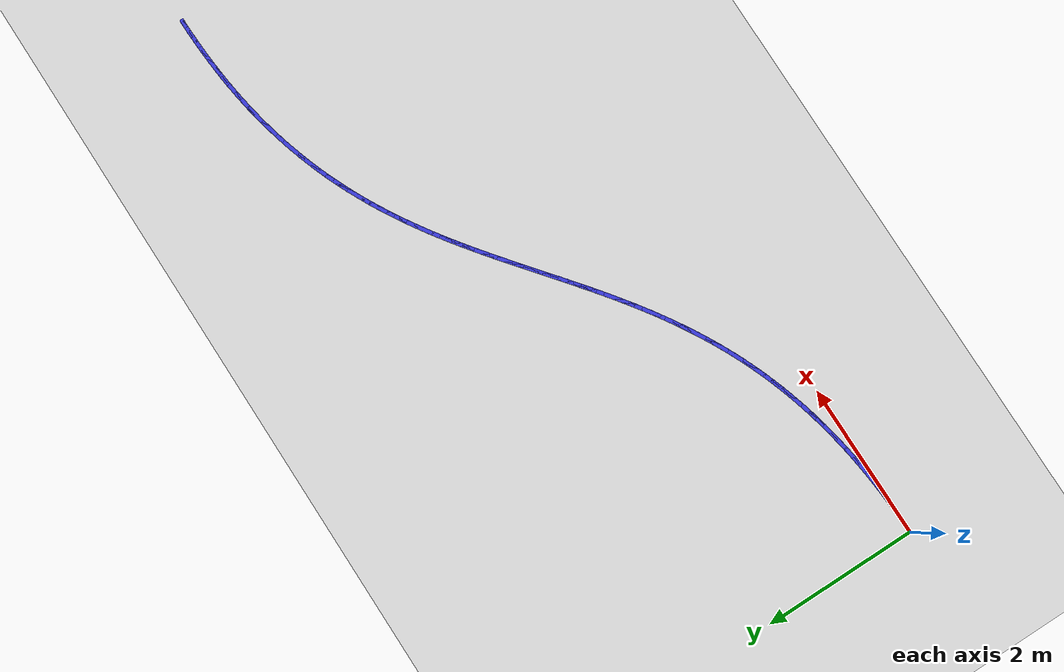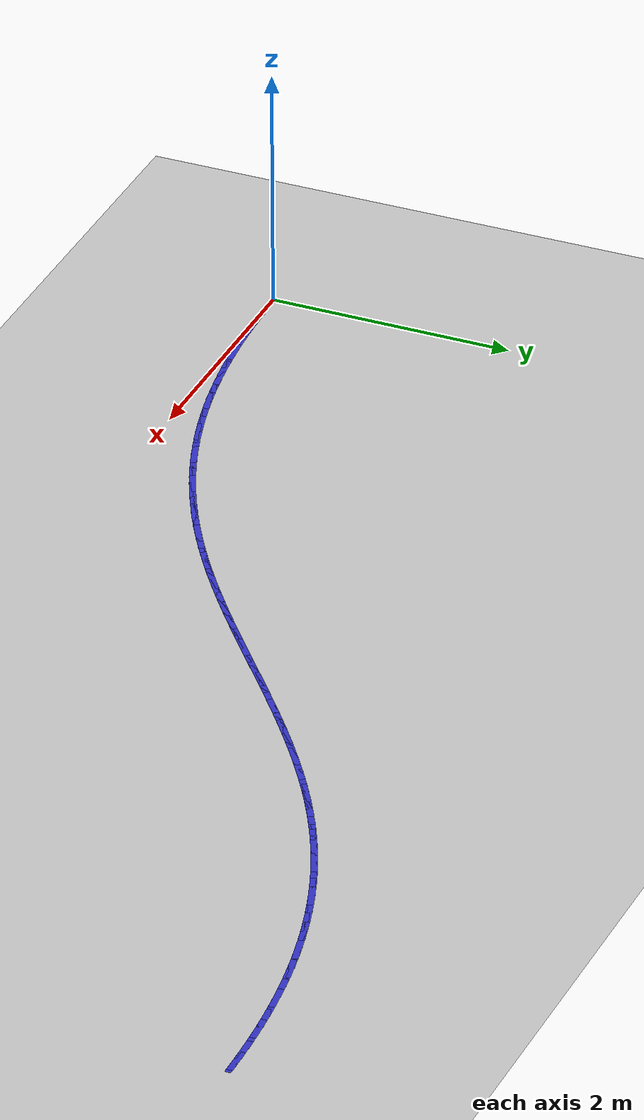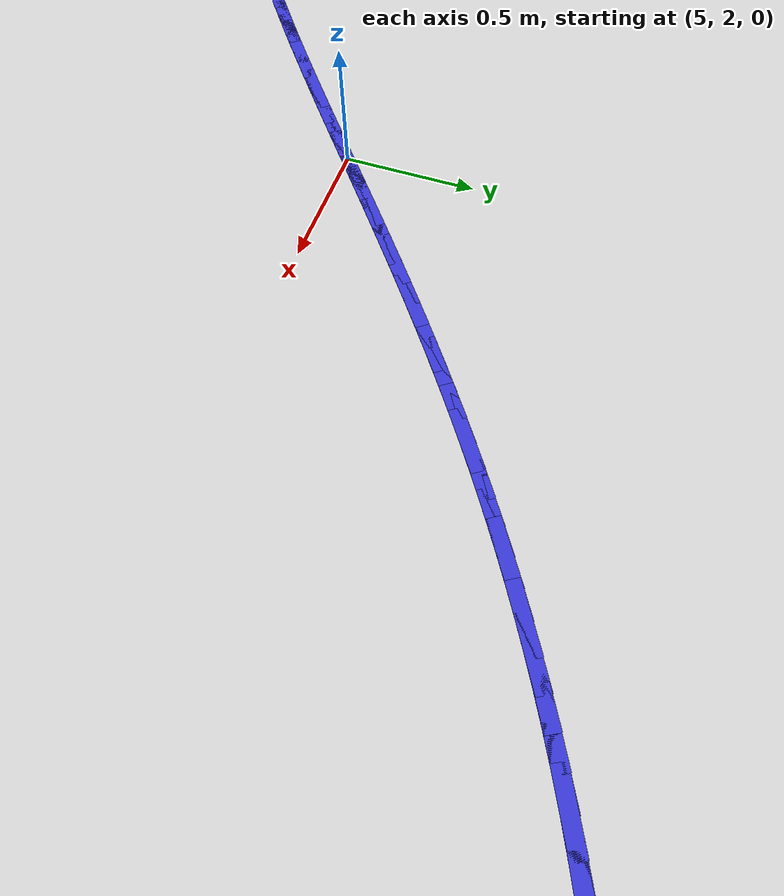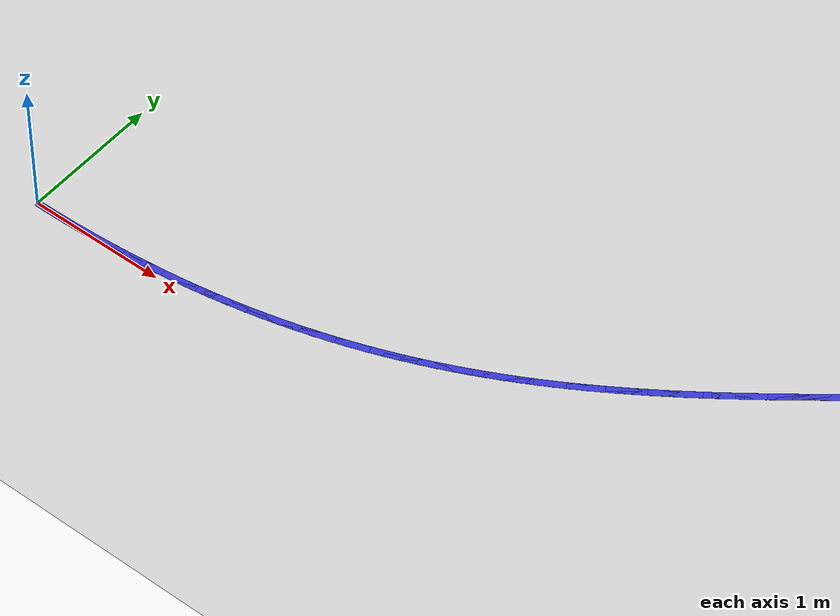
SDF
<sdf version='1.10'>
  <world name='empty'>
    <physics name='1ms' type='ignored'>
      <max_step_size>0.001</max_step_size>
      <real_time_factor>1</real_time_factor>
      <real_time_update_rate>1000</real_time_update_rate>
    </physics>
    <plugin name='gz::sim::systems::Physics' filename='gz-sim-physics-system'/>
    <plugin name='gz::sim::systems::UserCommands' filename='gz-sim-user-commands-system'/>
    <plugin name='gz::sim::systems::SceneBroadcaster' filename='gz-sim-scene-broadcaster-system'/>
    <plugin name='gz::sim::systems::Contact' filename='gz-sim-contact-system'/>
    <gravity>0 0 -9.8000000000000007</gravity>
    <magnetic_field>5.5644999999999998e-06 2.2875799999999999e-05 -4.2388400000000002e-05</magnetic_field>
    <atmosphere type='adiabatic'/>
    <scene>
      <ambient>0.400000006 0.400000006 0.400000006 1</ambient>
      <background>0.699999988 0.699999988 0.699999988 1</background>
      <shadows>true</shadows>
    </scene>
    <model name='ground_plane'>
      <static>true</static>
      <link name='link'>
        <collision name='collision'>
          <geometry>
            <plane>
              <normal>0 0 1</normal>
              <size>100 100</size>
            </plane>
          </geometry>
          <surface>
            <friction>
              <ode/>
            </friction>
            <bounce/>
            <contact/>
          </surface>
        </collision>
        <visual name='visual'>
          <geometry>
            <plane>
              <normal>0 0 1</normal>
              <size>100 100</size>
            </plane>
          </geometry>
          <material>
            <ambient>0.800000012 0.800000012 0.800000012 1</ambient>
            <diffuse>0.800000012 0.800000012 0.800000012 1</diffuse>
            <specular>0.800000012 0.800000012 0.800000012 1</specular>
          </material>
        </visual>
        <pose>0 0 0 0 0 0</pose>
        <inertial>
          <pose>0 0 0 0 0 0</pose>
          <mass>1</mass>
          <inertia>
            <ixx>1</ixx>
            <ixy>0</ixy>
            <ixz>0</ixz>
            <iyy>1</iyy>
            <iyz>0</iyz>
            <izz>1</izz>
          </inertia>
        </inertial>
        <enable_wind>false</enable_wind>
      </link>
      <pose>0 0 0 0 0 0</pose>
      <self_collide>false</self_collide>
    </model>

    <model name='unit_box_0'>
      <link name='box_link'>
        <collision name='box_collision'>
          <geometry>
            <box>
              <size>0.000005 0.000005 0.000005</size>
            </box>
          </geometry>
          <surface>
            <friction>
              <ode/>
            </friction>
            <bounce/>
            <contact/>
          </surface>
        </collision>
        <visual name='box_visual'>
          <geometry>
            <box>
              <size>0.12 0.05 0.0005</size>
            </box>
          </geometry>
          <material>
            <ambient>0.300000012 0.300000012 0.300000012 1</ambient>
            <diffuse>0.2 0.2 0.8 1</diffuse>
            <specular>1 1 1 1</specular>
          </material>
        </visual>
        <pose>0.06 0.0 0 0 0 0.0</pose>
        <enable_wind>false</enable_wind>
      </link>
      <static>false</static>
      <self_collide>false</self_collide>
    </model>

    <model name='unit_box_1'>
      <link name='box_link'>
        <collision name='box_collision'>
          <geometry>
            <box>
              <size>0.000005 0.000005 0.000005</size>
            </box>
          </geometry>
          <surface>
            <friction>
              <ode/>
            </friction>
            <bounce/>
            <contact/>
          </surface>
        </collision>
        <visual name='box_visual'>
          <geometry>
            <box>
              <size>0.24 0.05 0.0005</size>
            </box>
          </geometry>
          <material>
            <ambient>0.300000012 0.300000012 0.300000012 1</ambient>
            <diffuse>0.2 0.2 0.8 1</diffuse>
            <specular>1 1 1 1</specular>
          </material>
        </visual>
        <pose>0.1499950015407622 0.0012161199795114705 0 0 0 0.008107559056602417</pose>
        <enable_wind>false</enable_wind>
      </link>
      <static>false</static>
      <self_collide>false</self_collide>
    </model>

    <model name='unit_box_2'>
      <link name='box_link'>
        <collision name='box_collision'>
          <geometry>
            <box>
              <size>0.000005 0.000005 0.000005</size>
            </box>
          </geometry>
          <surface>
            <friction>
              <ode/>
            </friction>
            <bounce/>
            <contact/>
          </surface>
        </collision>
        <visual name='box_visual'>
          <geometry>
            <box>
              <size>0.24 0.05 0.0005</size>
            </box>
          </geometry>
          <material>
            <ambient>0.300000012 0.300000012 0.300000012 1</ambient>
            <diffuse>0.2 0.2 0.8 1</diffuse>
            <specular>1 1 1 1</specular>
          </material>
        </visual>
        <pose>0.29699092753883083 0.004831500393177774 0 0 0 0.024590148667046275</pose>
        <enable_wind>false</enable_wind>
      </link>
      <static>false</static>
      <self_collide>false</self_collide>
    </model>

    <model name='unit_box_3'>
      <link name='box_link'>
        <collision name='box_collision'>
          <geometry>
            <box>
              <size>0.000005 0.000005 0.000005</size>
            </box>
          </geometry>
          <surface>
            <friction>
              <ode/>
            </friction>
            <bounce/>
            <contact/>
          </surface>
        </collision>
        <visual name='box_visual'>
          <geometry>
            <box>
              <size>0.24 0.05 0.0005</size>
            </box>
          </geometry>
          <material>
            <ambient>0.300000012 0.300000012 0.300000012 1</ambient>
            <diffuse>0.2 0.2 0.8 1</diffuse>
            <specular>1 1 1 1</specular>
          </material>
        </visual>
        <pose>0.4410496146033337 0.010796671953696747 0 0 0 0.04138428482263463</pose>
        <enable_wind>false</enable_wind>
      </link>
      <static>false</static>
      <self_collide>false</self_collide>
    </model>

    <model name='unit_box_4'>
      <link name='box_link'>
        <collision name='box_collision'>
          <geometry>
            <box>
              <size>0.000005 0.000005 0.000005</size>
            </box>
          </geometry>
          <surface>
            <friction>
              <ode/>
            </friction>
            <bounce/>
            <contact/>
          </surface>
        </collision>
        <visual name='box_visual'>
          <geometry>
            <box>
              <size>0.24 0.05 0.0005</size>
            </box>
          </geometry>
          <material>
            <ambient>0.300000012 0.300000012 0.300000012 1</ambient>
            <diffuse>0.2 0.2 0.8 1</diffuse>
            <specular>1 1 1 1</specular>
          </material>
        </visual>
        <pose>0.5822328993433984 0.019062165373766232 0 0 0 0.058477670509446376</pose>
        <enable_wind>false</enable_wind>
      </link>
      <static>false</static>
      <self_collide>false</self_collide>
    </model>

    <model name='unit_box_5'>
      <link name='box_link'>
        <collision name='box_collision'>
          <geometry>
            <box>
              <size>0.000005 0.000005 0.000005</size>
            </box>
          </geometry>
          <surface>
            <friction>
              <ode/>
            </friction>
            <bounce/>
            <contact/>
          </surface>
        </collision>
        <visual name='box_visual'>
          <geometry>
            <box>
              <size>0.24 0.05 0.0005</size>
            </box>
          </geometry>
          <material>
            <ambient>0.300000012 0.300000012 0.300000012 1</ambient>
            <diffuse>0.2 0.2 0.8 1</diffuse>
            <specular>1 1 1 1</specular>
          </material>
        </visual>
        <pose>0.7206026183681526 0.029578511366084064 0 0 0 0.07585595699928427</pose>
        <enable_wind>false</enable_wind>
      </link>
      <static>false</static>
      <self_collide>false</self_collide>
    </model>

    <model name='unit_box_6'>
      <link name='box_link'>
        <collision name='box_collision'>
          <geometry>
            <box>
              <size>0.000005 0.000005 0.000005</size>
            </box>
          </geometry>
          <surface>
            <friction>
              <ode/>
            </friction>
            <bounce/>
            <contact/>
          </surface>
        </collision>
        <visual name='box_visual'>
          <geometry>
            <box>
              <size>0.24 0.05 0.0005</size>
            </box>
          </geometry>
          <material>
            <ambient>0.300000012 0.300000012 0.300000012 1</ambient>
            <diffuse>0.2 0.2 0.8 1</diffuse>
            <specular>1 1 1 1</specular>
          </material>
        </visual>
        <pose>0.8562206082867242 0.04229624064334808 0 0 0 0.0935026763067745</pose>
        <enable_wind>false</enable_wind>
      </link>
      <static>false</static>
      <self_collide>false</self_collide>
    </model>

    <model name='unit_box_7'>
      <link name='box_link'>
        <collision name='box_collision'>
          <geometry>
            <box>
              <size>0.000005 0.000005 0.000005</size>
            </box>
          </geometry>
          <surface>
            <friction>
              <ode/>
            </friction>
            <bounce/>
            <contact/>
          </surface>
        </collision>
        <visual name='box_visual'>
          <geometry>
            <box>
              <size>0.24 0.05 0.0005</size>
            </box>
          </geometry>
          <material>
            <ambient>0.300000012 0.300000012 0.300000012 1</ambient>
            <diffuse>0.2 0.2 0.8 1</diffuse>
            <specular>1 1 1 1</specular>
          </material>
        </visual>
        <pose>0.9891487057082403 0.05716588391825612 0 0 0 0.11139919209406075</pose>
        <enable_wind>false</enable_wind>
      </link>
      <static>false</static>
      <self_collide>false</self_collide>
    </model>

    <model name='unit_box_8'>
      <link name='box_link'>
        <collision name='box_collision'>
          <geometry>
            <box>
              <size>0.000005 0.000005 0.000005</size>
            </box>
          </geometry>
          <surface>
            <friction>
              <ode/>
            </friction>
            <bounce/>
            <contact/>
          </surface>
        </collision>
        <visual name='box_visual'>
          <geometry>
            <box>
              <size>0.24 0.05 0.0005</size>
            </box>
          </geometry>
          <material>
            <ambient>0.300000012 0.300000012 0.300000012 1</ambient>
            <diffuse>0.2 0.2 0.8 1</diffuse>
            <specular>1 1 1 1</specular>
          </material>
        </visual>
        <pose>1.1194487472418297 0.07413797190350604 0 0 0 0.12952467185254574</pose>
        <enable_wind>false</enable_wind>
      </link>
      <static>false</static>
      <self_collide>false</self_collide>
    </model>

    <model name='unit_box_9'>
      <link name='box_link'>
        <collision name='box_collision'>
          <geometry>
            <box>
              <size>0.000005 0.000005 0.000005</size>
            </box>
          </geometry>
          <surface>
            <friction>
              <ode/>
            </friction>
            <bounce/>
            <contact/>
          </surface>
        </collision>
        <visual name='box_visual'>
          <geometry>
            <box>
              <size>0.24 0.05 0.0005</size>
            </box>
          </geometry>
          <material>
            <ambient>0.300000012 0.300000012 0.300000012 1</ambient>
            <diffuse>0.2 0.2 0.8 1</diffuse>
            <specular>1 1 1 1</specular>
          </material>
        </visual>
        <pose>1.247182569496619 0.09316303531179564 0 0 0 0.14785608298010453</pose>
        <enable_wind>false</enable_wind>
      </link>
      <static>false</static>
      <self_collide>false</self_collide>
    </model>

    <model name='unit_box_10'>
      <link name='box_link'>
        <collision name='box_collision'>
          <geometry>
            <box>
              <size>0.000005 0.000005 0.000005</size>
            </box>
          </geometry>
          <surface>
            <friction>
              <ode/>
            </friction>
            <bounce/>
            <contact/>
          </surface>
        </collision>
        <visual name='box_visual'>
          <geometry>
            <box>
              <size>0.24 0.05 0.0005</size>
            </box>
          </geometry>
          <material>
            <ambient>0.300000012 0.300000012 0.300000012 1</ambient>
            <diffuse>0.2 0.2 0.8 1</diffuse>
            <specular>1 1 1 1</specular>
          </material>
        </visual>
        <pose>1.3724120090817367 0.11419160485582279 0 0 0 0.16636821504002</pose>
        <enable_wind>false</enable_wind>
      </link>
      <static>false</static>
      <self_collide>false</self_collide>
    </model>

    <model name='unit_box_11'>
      <link name='box_link'>
        <collision name='box_collision'>
          <geometry>
            <box>
              <size>0.000005 0.000005 0.000005</size>
            </box>
          </geometry>
          <surface>
            <friction>
              <ode/>
            </friction>
            <bounce/>
            <contact/>
          </surface>
        </collision>
        <visual name='box_visual'>
          <geometry>
            <box>
              <size>0.24 0.05 0.0005</size>
            </box>
          </geometry>
          <material>
            <ambient>0.300000012 0.300000012 0.300000012 1</ambient>
            <diffuse>0.2 0.2 0.8 1</diffuse>
            <specular>1 1 1 1</specular>
          </material>
        </visual>
        <pose>1.4951989026063097 0.1371742112482853 0 0 0 0.18503373003178222</pose>
        <enable_wind>false</enable_wind>
      </link>
      <static>false</static>
      <self_collide>false</self_collide>
    </model>

    <model name='unit_box_12'>
      <link name='box_link'>
        <collision name='box_collision'>
          <geometry>
            <box>
              <size>0.000005 0.000005 0.000005</size>
            </box>
          </geometry>
          <surface>
            <friction>
              <ode/>
            </friction>
            <bounce/>
            <contact/>
          </surface>
        </collision>
        <visual name='box_visual'>
          <geometry>
            <box>
              <size>0.24 0.05 0.0005</size>
            </box>
          </geometry>
          <material>
            <ambient>0.300000012 0.300000012 0.300000012 1</ambient>
            <diffuse>0.2 0.2 0.8 1</diffuse>
            <specular>1 1 1 1</specular>
          </material>
        </visual>
        <pose>1.615605086679467 0.16206138520188107 0 0 0 0.2038232419275935</pose>
        <enable_wind>false</enable_wind>
      </link>
      <static>false</static>
      <self_collide>false</self_collide>
    </model>

    <model name='unit_box_13'>
      <link name='box_link'>
        <collision name='box_collision'>
          <geometry>
            <box>
              <size>0.000005 0.000005 0.000005</size>
            </box>
          </geometry>
          <surface>
            <friction>
              <ode/>
            </friction>
            <bounce/>
            <contact/>
          </surface>
        </collision>
        <visual name='box_visual'>
          <geometry>
            <box>
              <size>0.24 0.05 0.0005</size>
            </box>
          </geometry>
          <material>
            <ambient>0.300000012 0.300000012 0.300000012 1</ambient>
            <diffuse>0.2 0.2 0.8 1</diffuse>
            <specular>1 1 1 1</specular>
          </material>
        </visual>
        <pose>1.7336923979103354 0.18880365742930794 0 0 0 0.22270542604355534</pose>
        <enable_wind>false</enable_wind>
      </link>
      <static>false</static>
      <self_collide>false</self_collide>
    </model>

    <model name='unit_box_14'>
      <link name='box_link'>
        <collision name='box_collision'>
          <geometry>
            <box>
              <size>0.000005 0.000005 0.000005</size>
            </box>
          </geometry>
          <surface>
            <friction>
              <ode/>
            </friction>
            <bounce/>
            <contact/>
          </surface>
        </collision>
        <visual name='box_visual'>
          <geometry>
            <box>
              <size>0.24 0.05 0.0005</size>
            </box>
          </geometry>
          <material>
            <ambient>0.300000012 0.300000012 0.300000012 1</ambient>
            <diffuse>0.2 0.2 0.8 1</diffuse>
            <specular>1 1 1 1</specular>
          </material>
        </visual>
        <pose>1.8495226729080412 0.21735155864326353 0 0 0 0.24164715804040357</pose>
        <enable_wind>false</enable_wind>
      </link>
      <static>false</static>
      <self_collide>false</self_collide>
    </model>

    <model name='unit_box_15'>
      <link name='box_link'>
        <collision name='box_collision'>
          <geometry>
            <box>
              <size>0.000005 0.000005 0.000005</size>
            </box>
          </geometry>
          <surface>
            <friction>
              <ode/>
            </friction>
            <bounce/>
            <contact/>
          </surface>
        </collision>
        <visual name='box_visual'>
          <geometry>
            <box>
              <size>0.24 0.05 0.0005</size>
            </box>
          </geometry>
          <material>
            <ambient>0.300000012 0.300000012 0.300000012 1</ambient>
            <diffuse>0.2 0.2 0.8 1</diffuse>
            <specular>1 1 1 1</specular>
          </material>
        </visual>
        <pose>1.9631577482817155 0.24765561955644602 0 0 0 0.26061368151271525</pose>
        <enable_wind>false</enable_wind>
      </link>
      <static>false</static>
      <self_collide>false</self_collide>
    </model>

    <model name='unit_box_16'>
      <link name='box_link'>
        <collision name='box_collision'>
          <geometry>
            <box>
              <size>0.000005 0.000005 0.000005</size>
            </box>
          </geometry>
          <surface>
            <friction>
              <ode/>
            </friction>
            <bounce/>
            <contact/>
          </surface>
        </collision>
        <visual name='box_visual'>
          <geometry>
            <box>
              <size>0.24 0.05 0.0005</size>
            </box>
          </geometry>
          <material>
            <ambient>0.300000012 0.300000012 0.300000012 1</ambient>
            <diffuse>0.2 0.2 0.8 1</diffuse>
            <specular>1 1 1 1</specular>
          </material>
        </visual>
        <pose>2.0746594606404827 0.27966637088155305 0 0 0 0.27956880226170633</pose>
        <enable_wind>false</enable_wind>
      </link>
      <static>false</static>
      <self_collide>false</self_collide>
    </model>

    <model name='unit_box_17'>
      <link name='box_link'>
        <collision name='box_collision'>
          <geometry>
            <box>
              <size>0.000005 0.000005 0.000005</size>
            </box>
          </geometry>
          <surface>
            <friction>
              <ode/>
            </friction>
            <bounce/>
            <contact/>
          </surface>
        </collision>
        <visual name='box_visual'>
          <geometry>
            <box>
              <size>0.24 0.05 0.0005</size>
            </box>
          </geometry>
          <material>
            <ambient>0.300000012 0.300000012 0.300000012 1</ambient>
            <diffuse>0.2 0.2 0.8 1</diffuse>
            <specular>1 1 1 1</specular>
          </material>
        </visual>
        <pose>2.1840896465934727 0.3133343433312824 0 0 0 0.29847510649412506</pose>
        <enable_wind>false</enable_wind>
      </link>
      <static>false</static>
      <self_collide>false</self_collide>
    </model>

    <model name='unit_box_18'>
      <link name='box_link'>
        <collision name='box_collision'>
          <geometry>
            <box>
              <size>0.000005 0.000005 0.000005</size>
            </box>
          </geometry>
          <surface>
            <friction>
              <ode/>
            </friction>
            <bounce/>
            <contact/>
          </surface>
        </collision>
        <visual name='box_visual'>
          <geometry>
            <box>
              <size>0.24 0.05 0.0005</size>
            </box>
          </geometry>
          <material>
            <ambient>0.300000012 0.300000012 0.300000012 1</ambient>
            <diffuse>0.2 0.2 0.8 1</diffuse>
            <specular>1 1 1 1</specular>
          </material>
        </visual>
        <pose>2.2915101427498112 0.348610067618332 0 0 0 0.31729419939076314</pose>
        <enable_wind>false</enable_wind>
      </link>
      <static>false</static>
      <self_collide>false</self_collide>
    </model>

    <model name='unit_box_19'>
      <link name='box_link'>
        <collision name='box_collision'>
          <geometry>
            <box>
              <size>0.000005 0.000005 0.000005</size>
            </box>
          </geometry>
          <surface>
            <friction>
              <ode/>
            </friction>
            <bounce/>
            <contact/>
          </surface>
        </collision>
        <visual name='box_visual'>
          <geometry>
            <box>
              <size>0.24 0.05 0.0005</size>
            </box>
          </geometry>
          <material>
            <ambient>0.300000012 0.300000012 0.300000012 1</ambient>
            <diffuse>0.2 0.2 0.8 1</diffuse>
            <specular>1 1 1 1</specular>
          </material>
        </visual>
        <pose>2.3969827857186283 0.38544407445539974 0 0 0 0.33598695978376614</pose>
        <enable_wind>false</enable_wind>
      </link>
      <static>false</static>
      <self_collide>false</self_collide>
    </model>

    <model name='unit_box_20'>
      <link name='box_link'>
        <collision name='box_collision'>
          <geometry>
            <box>
              <size>0.000005 0.000005 0.000005</size>
            </box>
          </geometry>
          <surface>
            <friction>
              <ode/>
            </friction>
            <bounce/>
            <contact/>
          </surface>
        </collision>
        <visual name='box_visual'>
          <geometry>
            <box>
              <size>0.24 0.05 0.0005</size>
            </box>
          </geometry>
          <material>
            <ambient>0.300000012 0.300000012 0.300000012 1</ambient>
            <diffuse>0.2 0.2 0.8 1</diffuse>
            <specular>1 1 1 1</specular>
          </material>
        </visual>
        <pose>2.500569412109051 0.42378689455518354 0 0 0 0.3545138061122166</pose>
        <enable_wind>false</enable_wind>
      </link>
      <static>false</static>
      <self_collide>false</self_collide>
    </model>

    <model name='unit_box_21'>
      <link name='box_link'>
        <collision name='box_collision'>
          <geometry>
            <box>
              <size>0.000005 0.000005 0.000005</size>
            </box>
          </geometry>
          <surface>
            <friction>
              <ode/>
            </friction>
            <bounce/>
            <contact/>
          </surface>
        </collision>
        <visual name='box_visual'>
          <geometry>
            <box>
              <size>0.24 0.05 0.0005</size>
            </box>
          </geometry>
          <material>
            <ambient>0.300000012 0.300000012 0.300000012 1</ambient>
            <diffuse>0.2 0.2 0.8 1</diffuse>
            <specular>1 1 1 1</specular>
          </material>
        </visual>
        <pose>2.6023318585302055 0.463589058630381 0 0 0 0.3728349684215813</pose>
        <enable_wind>false</enable_wind>
      </link>
      <static>false</static>
      <self_collide>false</self_collide>
    </model>

    <model name='unit_box_22'>
      <link name='box_link'>
        <collision name='box_collision'>
          <geometry>
            <box>
              <size>0.000005 0.000005 0.000005</size>
            </box>
          </geometry>
          <surface>
            <friction>
              <ode/>
            </friction>
            <bounce/>
            <contact/>
          </surface>
        </collision>
        <visual name='box_visual'>
          <geometry>
            <box>
              <size>0.24 0.05 0.0005</size>
            </box>
          </geometry>
          <material>
            <ambient>0.300000012 0.300000012 0.300000012 1</ambient>
            <diffuse>0.2 0.2 0.8 1</diffuse>
            <specular>1 1 1 1</specular>
          </material>
        </visual>
        <pose>2.702331961591221 0.50480109739369 0 0 0 0.3909107609597008</pose>
        <enable_wind>false</enable_wind>
      </link>
      <static>false</static>
      <self_collide>false</self_collide>
    </model>

    <model name='unit_box_23'>
      <link name='box_link'>
        <collision name='box_collision'>
          <geometry>
            <box>
              <size>0.000005 0.000005 0.000005</size>
            </box>
          </geometry>
          <surface>
            <friction>
              <ode/>
            </friction>
            <bounce/>
            <contact/>
          </surface>
        </collision>
        <visual name='box_visual'>
          <geometry>
            <box>
              <size>0.24 0.05 0.0005</size>
            </box>
          </geometry>
          <material>
            <ambient>0.300000012 0.300000012 0.300000012 1</ambient>
            <diffuse>0.2 0.2 0.8 1</diffuse>
            <specular>1 1 1 1</specular>
          </material>
        </visual>
        <pose>2.800631557901225 0.5473735415578085 0 0 0 0.40870184991191016</pose>
        <enable_wind>false</enable_wind>
      </link>
      <static>false</static>
      <self_collide>false</self_collide>
    </model>

    <model name='unit_box_24'>
      <link name='box_link'>
        <collision name='box_collision'>
          <geometry>
            <box>
              <size>0.000005 0.000005 0.000005</size>
            </box>
          </geometry>
          <surface>
            <friction>
              <ode/>
            </friction>
            <bounce/>
            <contact/>
          </surface>
        </collision>
        <visual name='box_visual'>
          <geometry>
            <box>
              <size>0.24 0.05 0.0005</size>
            </box>
          </geometry>
          <material>
            <ambient>0.300000012 0.300000012 0.300000012 1</ambient>
            <diffuse>0.2 0.2 0.8 1</diffuse>
            <specular>1 1 1 1</specular>
          </material>
        </visual>
        <pose>2.8972924840693435 0.5912569218354342 0 0 0 0.4261695110121677</pose>
        <enable_wind>false</enable_wind>
      </link>
      <static>false</static>
      <self_collide>false</self_collide>
    </model>

    <model name='unit_box_25'>
      <link name='box_link'>
        <collision name='box_collision'>
          <geometry>
            <box>
              <size>0.000005 0.000005 0.000005</size>
            </box>
          </geometry>
          <surface>
            <friction>
              <ode/>
            </friction>
            <bounce/>
            <contact/>
          </surface>
        </collision>
        <visual name='box_visual'>
          <geometry>
            <box>
              <size>0.24 0.05 0.0005</size>
            </box>
          </geometry>
          <material>
            <ambient>0.300000012 0.300000012 0.300000012 1</ambient>
            <diffuse>0.2 0.2 0.8 1</diffuse>
            <specular>1 1 1 1</specular>
          </material>
        </visual>
        <pose>2.992376576704706 0.6364017689392651 0 0 0 0.4432758721547199</pose>
        <enable_wind>false</enable_wind>
      </link>
      <static>false</static>
      <self_collide>false</self_collide>
    </model>

    <model name='unit_box_26'>
      <link name='box_link'>
        <collision name='box_collision'>
          <geometry>
            <box>
              <size>0.000005 0.000005 0.000005</size>
            </box>
          </geometry>
          <surface>
            <friction>
              <ode/>
            </friction>
            <bounce/>
            <contact/>
          </surface>
        </collision>
        <visual name='box_visual'>
          <geometry>
            <box>
              <size>0.24 0.05 0.0005</size>
            </box>
          </geometry>
          <material>
            <ambient>0.300000012 0.300000012 0.300000012 1</ambient>
            <diffuse>0.2 0.2 0.8 1</diffuse>
            <specular>1 1 1 1</specular>
          </material>
        </visual>
        <pose>3.0859456724164414 0.6827586135819992 0 0 0 0.4599841366895155</pose>
        <enable_wind>false</enable_wind>
      </link>
      <static>false</static>
      <self_collide>false</self_collide>
    </model>

    <model name='unit_box_27'>
      <link name='box_link'>
        <collision name='box_collision'>
          <geometry>
            <box>
              <size>0.000005 0.000005 0.000005</size>
            </box>
          </geometry>
          <surface>
            <friction>
              <ode/>
            </friction>
            <bounce/>
            <contact/>
          </surface>
        </collision>
        <visual name='box_visual'>
          <geometry>
            <box>
              <size>0.24 0.05 0.0005</size>
            </box>
          </geometry>
          <material>
            <ambient>0.300000012 0.300000012 0.300000012 1</ambient>
            <diffuse>0.2 0.2 0.8 1</diffuse>
            <specular>1 1 1 1</specular>
          </material>
        </visual>
        <pose>3.1780616078136736 0.7302779864763335 0 0 0 0.47625878378315817</pose>
        <enable_wind>false</enable_wind>
      </link>
      <static>false</static>
      <self_collide>false</self_collide>
    </model>

    <model name='unit_box_28'>
      <link name='box_link'>
        <collision name='box_collision'>
          <geometry>
            <box>
              <size>0.000005 0.000005 0.000005</size>
            </box>
          </geometry>
          <surface>
            <friction>
              <ode/>
            </friction>
            <bounce/>
            <contact/>
          </surface>
        </collision>
        <visual name='box_visual'>
          <geometry>
            <box>
              <size>0.24 0.05 0.0005</size>
            </box>
          </geometry>
          <material>
            <ambient>0.300000012 0.300000012 0.300000012 1</ambient>
            <diffuse>0.2 0.2 0.8 1</diffuse>
            <specular>1 1 1 1</specular>
          </material>
        </visual>
        <pose>3.2687862195055333 0.7789104183349667 0 0 0 0.4920657430277577</pose>
        <enable_wind>false</enable_wind>
      </link>
      <static>false</static>
      <self_collide>false</self_collide>
    </model>

    <model name='unit_box_29'>
      <link name='box_link'>
        <collision name='box_collision'>
          <geometry>
            <box>
              <size>0.000005 0.000005 0.000005</size>
            </box>
          </geometry>
          <surface>
            <friction>
              <ode/>
            </friction>
            <bounce/>
            <contact/>
          </surface>
        </collision>
        <visual name='box_visual'>
          <geometry>
            <box>
              <size>0.24 0.05 0.0005</size>
            </box>
          </geometry>
          <material>
            <ambient>0.300000012 0.300000012 0.300000012 1</ambient>
            <diffuse>0.2 0.2 0.8 1</diffuse>
            <specular>1 1 1 1</specular>
          </material>
        </visual>
        <pose>3.3581813441011485 0.8286064398705966 0 0 0 0.5073725413413152</pose>
        <enable_wind>false</enable_wind>
      </link>
      <static>false</static>
      <self_collide>false</self_collide>
    </model>

    <model name='unit_box_30'>
      <link name='box_link'>
        <collision name='box_collision'>
          <geometry>
            <box>
              <size>0.000005 0.000005 0.000005</size>
            </box>
          </geometry>
          <surface>
            <friction>
              <ode/>
            </friction>
            <bounce/>
            <contact/>
          </surface>
        </collision>
        <visual name='box_visual'>
          <geometry>
            <box>
              <size>0.24 0.05 0.0005</size>
            </box>
          </geometry>
          <material>
            <ambient>0.300000012 0.300000012 0.300000012 1</ambient>
            <diffuse>0.2 0.2 0.8 1</diffuse>
            <specular>1 1 1 1</specular>
          </material>
        </visual>
        <pose>3.446308818209646 0.8793165817959208 0 0 0 0.522148421082413</pose>
        <enable_wind>false</enable_wind>
      </link>
      <static>false</static>
      <self_collide>false</self_collide>
    </model>

    <model name='unit_box_31'>
      <link name='box_link'>
        <collision name='box_collision'>
          <geometry>
            <box>
              <size>0.000005 0.000005 0.000005</size>
            </box>
          </geometry>
          <surface>
            <friction>
              <ode/>
            </friction>
            <bounce/>
            <contact/>
          </surface>
        </collision>
        <visual name='box_visual'>
          <geometry>
            <box>
              <size>0.24 0.05 0.0005</size>
            </box>
          </geometry>
          <material>
            <ambient>0.300000012 0.300000012 0.300000012 1</ambient>
            <diffuse>0.2 0.2 0.8 1</diffuse>
            <specular>1 1 1 1</specular>
          </material>
        </visual>
        <pose>3.533230478440151 0.9309913748236369 0 0 0 0.5363644291603314</pose>
        <enable_wind>false</enable_wind>
      </link>
      <static>false</static>
      <self_collide>false</self_collide>
    </model>

    <model name='unit_box_32'>
      <link name='box_link'>
        <collision name='box_collision'>
          <geometry>
            <box>
              <size>0.000005 0.000005 0.000005</size>
            </box>
          </geometry>
          <surface>
            <friction>
              <ode/>
            </friction>
            <bounce/>
            <contact/>
          </surface>
        </collision>
        <visual name='box_visual'>
          <geometry>
            <box>
              <size>0.24 0.05 0.0005</size>
            </box>
          </geometry>
          <material>
            <ambient>0.300000012 0.300000012 0.300000012 1</ambient>
            <diffuse>0.2 0.2 0.8 1</diffuse>
            <specular>1 1 1 1</specular>
          </material>
        </visual>
        <pose>3.619008161401794 0.9835813496664431 0 0 0 0.5499934777234783</pose>
        <enable_wind>false</enable_wind>
      </link>
      <static>false</static>
      <self_collide>false</self_collide>
    </model>

    <model name='unit_box_33'>
      <link name='box_link'>
        <collision name='box_collision'>
          <geometry>
            <box>
              <size>0.000005 0.000005 0.000005</size>
            </box>
          </geometry>
          <surface>
            <friction>
              <ode/>
            </friction>
            <bounce/>
            <contact/>
          </surface>
        </collision>
        <visual name='box_visual'>
          <geometry>
            <box>
              <size>0.24 0.05 0.0005</size>
            </box>
          </geometry>
          <material>
            <ambient>0.300000012 0.300000012 0.300000012 1</ambient>
            <diffuse>0.2 0.2 0.8 1</diffuse>
            <specular>1 1 1 1</specular>
          </material>
        </visual>
        <pose>3.703703703703704 1.037037037037037 0 0 0 0.5630103777263467</pose>
        <enable_wind>false</enable_wind>
      </link>
      <static>false</static>
      <self_collide>false</self_collide>
    </model>

    <model name='unit_box_34'>
      <link name='box_link'>
        <collision name='box_collision'>
          <geometry>
            <box>
              <size>0.000005 0.000005 0.000005</size>
            </box>
          </geometry>
          <surface>
            <friction>
              <ode/>
            </friction>
            <bounce/>
            <contact/>
          </surface>
        </collision>
        <visual name='box_visual'>
          <geometry>
            <box>
              <size>0.24 0.05 0.0005</size>
            </box>
          </geometry>
          <material>
            <ambient>0.300000012 0.300000012 0.300000012 1</ambient>
            <diffuse>0.2 0.2 0.8 1</diffuse>
            <specular>1 1 1 1</specular>
          </material>
        </visual>
        <pose>3.7873789419550055 1.0913089676481167 0 0 0 0.5753918472868415</pose>
        <enable_wind>false</enable_wind>
      </link>
      <static>false</static>
      <self_collide>false</self_collide>
    </model>

    <model name='unit_box_35'>
      <link name='box_link'>
        <collision name='box_collision'>
          <geometry>
            <box>
              <size>0.000005 0.000005 0.000005</size>
            </box>
          </geometry>
          <surface>
            <friction>
              <ode/>
            </friction>
            <bounce/>
            <contact/>
          </surface>
        </collision>
        <visual name='box_visual'>
          <geometry>
            <box>
              <size>0.24 0.05 0.0005</size>
            </box>
          </geometry>
          <material>
            <ambient>0.300000012 0.300000012 0.300000012 1</ambient>
            <diffuse>0.2 0.2 0.8 1</diffuse>
            <specular>1 1 1 1</specular>
          </material>
        </visual>
        <pose>3.8700957127648277 1.1463476722123798 0 0 0 0.5871164972395609</pose>
        <enable_wind>false</enable_wind>
      </link>
      <static>false</static>
      <self_collide>false</self_collide>
    </model>

    <model name='unit_box_36'>
      <link name='box_link'>
        <collision name='box_collision'>
          <geometry>
            <box>
              <size>0.000005 0.000005 0.000005</size>
            </box>
          </geometry>
          <surface>
            <friction>
              <ode/>
            </friction>
            <bounce/>
            <contact/>
          </surface>
        </collision>
        <visual name='box_visual'>
          <geometry>
            <box>
              <size>0.24 0.05 0.0005</size>
            </box>
          </geometry>
          <material>
            <ambient>0.300000012 0.300000012 0.300000012 1</ambient>
            <diffuse>0.2 0.2 0.8 1</diffuse>
            <specular>1 1 1 1</specular>
          </material>
        </visual>
        <pose>3.951915852742299 1.2021036814425246 0 0 0 0.598164796661388</pose>
        <enable_wind>false</enable_wind>
      </link>
      <static>false</static>
      <self_collide>false</self_collide>
    </model>

    <model name='unit_box_37'>
      <link name='box_link'>
        <collision name='box_collision'>
          <geometry>
            <box>
              <size>0.000005 0.000005 0.000005</size>
            </box>
          </geometry>
          <surface>
            <friction>
              <ode/>
            </friction>
            <bounce/>
            <contact/>
          </surface>
        </collision>
        <visual name='box_visual'>
          <geometry>
            <box>
              <size>0.24 0.05 0.0005</size>
            </box>
          </geometry>
          <material>
            <ambient>0.300000012 0.300000012 0.300000012 1</ambient>
            <diffuse>0.2 0.2 0.8 1</diffuse>
            <specular>1 1 1 1</specular>
          </material>
        </visual>
        <pose>4.032901198496547 1.2585275260512485 0 0 0 0.6085190213940487</pose>
        <enable_wind>false</enable_wind>
      </link>
      <static>false</static>
      <self_collide>false</self_collide>
    </model>

    <model name='unit_box_38'>
      <link name='box_link'>
        <collision name='box_collision'>
          <geometry>
            <box>
              <size>0.000005 0.000005 0.000005</size>
            </box>
          </geometry>
          <surface>
            <friction>
              <ode/>
            </friction>
            <bounce/>
            <contact/>
          </surface>
        </collision>
        <visual name='box_visual'>
          <geometry>
            <box>
              <size>0.24 0.05 0.0005</size>
            </box>
          </geometry>
          <material>
            <ambient>0.300000012 0.300000012 0.300000012 1</ambient>
            <diffuse>0.2 0.2 0.8 1</diffuse>
            <specular>1 1 1 1</specular>
          </material>
        </visual>
        <pose>4.113113586636696 1.3155697367512484 0 0 0 0.6181631887237502</pose>
        <enable_wind>false</enable_wind>
      </link>
      <static>false</static>
      <self_collide>false</self_collide>
    </model>

    <model name='unit_box_39'>
      <link name='box_link'>
        <collision name='box_collision'>
          <geometry>
            <box>
              <size>0.000005 0.000005 0.000005</size>
            </box>
          </geometry>
          <surface>
            <friction>
              <ode/>
            </friction>
            <bounce/>
            <contact/>
          </surface>
        </collision>
        <visual name='box_visual'>
          <geometry>
            <box>
              <size>0.24 0.05 0.0005</size>
            </box>
          </geometry>
          <material>
            <ambient>0.300000012 0.300000012 0.300000012 1</ambient>
            <diffuse>0.2 0.2 0.8 1</diffuse>
            <specular>1 1 1 1</specular>
          </material>
        </visual>
        <pose>4.192614853771879 1.3731808442552245 0 0 0 0.6270829814099572</pose>
        <enable_wind>false</enable_wind>
      </link>
      <static>false</static>
      <self_collide>false</self_collide>
    </model>

    <model name='unit_box_40'>
      <link name='box_link'>
        <collision name='box_collision'>
          <geometry>
            <box>
              <size>0.000005 0.000005 0.000005</size>
            </box>
          </geometry>
          <surface>
            <friction>
              <ode/>
            </friction>
            <bounce/>
            <contact/>
          </surface>
        </collision>
        <visual name='box_visual'>
          <geometry>
            <box>
              <size>0.24 0.05 0.0005</size>
            </box>
          </geometry>
          <material>
            <ambient>0.300000012 0.300000012 0.300000012 1</ambient>
            <diffuse>0.2 0.2 0.8 1</diffuse>
            <specular>1 1 1 1</specular>
          </material>
        </visual>
        <pose>4.2714668365112205 1.431311379275873 0 0 0 0.6352656642001349</pose>
        <enable_wind>false</enable_wind>
      </link>
      <static>false</static>
      <self_collide>false</self_collide>
    </model>

    <model name='unit_box_41'>
      <link name='box_link'>
        <collision name='box_collision'>
          <geometry>
            <box>
              <size>0.000005 0.000005 0.000005</size>
            </box>
          </geometry>
          <surface>
            <friction>
              <ode/>
            </friction>
            <bounce/>
            <contact/>
          </surface>
        </collision>
        <visual name='box_visual'>
          <geometry>
            <box>
              <size>0.24 0.05 0.0005</size>
            </box>
          </geometry>
          <material>
            <ambient>0.300000012 0.300000012 0.300000012 1</ambient>
            <diffuse>0.2 0.2 0.8 1</diffuse>
            <specular>1 1 1 1</specular>
          </material>
        </visual>
        <pose>4.349731371463848 1.4899118725258915 0 0 0 0.6426999958390573</pose>
        <enable_wind>false</enable_wind>
      </link>
      <static>false</static>
      <self_collide>false</self_collide>
    </model>

    <model name='unit_box_42'>
      <link name='box_link'>
        <collision name='box_collision'>
          <geometry>
            <box>
              <size>0.000005 0.000005 0.000005</size>
            </box>
          </geometry>
          <surface>
            <friction>
              <ode/>
            </friction>
            <bounce/>
            <contact/>
          </surface>
        </collision>
        <visual name='box_visual'>
          <geometry>
            <box>
              <size>0.24 0.05 0.0005</size>
            </box>
          </geometry>
          <material>
            <ambient>0.300000012 0.300000012 0.300000012 1</ambient>
            <diffuse>0.2 0.2 0.8 1</diffuse>
            <specular>1 1 1 1</specular>
          </material>
        </visual>
        <pose>4.427470295238891 1.5489328547179788 0 0 0 0.6493761393980781</pose>
        <enable_wind>false</enable_wind>
      </link>
      <static>false</static>
      <self_collide>false</self_collide>
    </model>

    <model name='unit_box_43'>
      <link name='box_link'>
        <collision name='box_collision'>
          <geometry>
            <box>
              <size>0.000005 0.000005 0.000005</size>
            </box>
          </geometry>
          <surface>
            <friction>
              <ode/>
            </friction>
            <bounce/>
            <contact/>
          </surface>
        </collision>
        <visual name='box_visual'>
          <geometry>
            <box>
              <size>0.24 0.05 0.0005</size>
            </box>
          </geometry>
          <material>
            <ambient>0.300000012 0.300000012 0.300000012 1</ambient>
            <diffuse>0.2 0.2 0.8 1</diffuse>
            <specular>1 1 1 1</specular>
          </material>
        </visual>
        <pose>4.504745444445475 1.608324856564832 0 0 0 0.6552855735250335</pose>
        <enable_wind>false</enable_wind>
      </link>
      <static>false</static>
      <self_collide>false</self_collide>
    </model>

    <model name='unit_box_44'>
      <link name='box_link'>
        <collision name='box_collision'>
          <geometry>
            <box>
              <size>0.000005 0.000005 0.000005</size>
            </box>
          </geometry>
          <surface>
            <friction>
              <ode/>
            </friction>
            <bounce/>
            <contact/>
          </surface>
        </collision>
        <visual name='box_visual'>
          <geometry>
            <box>
              <size>0.24 0.05 0.0005</size>
            </box>
          </geometry>
          <material>
            <ambient>0.300000012 0.300000012 0.300000012 1</ambient>
            <diffuse>0.2 0.2 0.8 1</diffuse>
            <specular>1 1 1 1</specular>
          </material>
        </visual>
        <pose>4.581618655692729 1.6680384087791493 0 0 0 0.6604210069645614</pose>
        <enable_wind>false</enable_wind>
      </link>
      <static>false</static>
      <self_collide>false</self_collide>
    </model>

    <model name='unit_box_45'>
      <link name='box_link'>
        <collision name='box_collision'>
          <geometry>
            <box>
              <size>0.000005 0.000005 0.000005</size>
            </box>
          </geometry>
          <surface>
            <friction>
              <ode/>
            </friction>
            <bounce/>
            <contact/>
          </surface>
        </collision>
        <visual name='box_visual'>
          <geometry>
            <box>
              <size>0.24 0.05 0.0005</size>
            </box>
          </geometry>
          <material>
            <ambient>0.300000012 0.300000012 0.300000012 1</ambient>
            <diffuse>0.2 0.2 0.8 1</diffuse>
            <specular>1 1 1 1</specular>
          </material>
        </visual>
        <pose>4.658151765589781 1.7280240420736286 0 0 0 0.6647762984325143</pose>
        <enable_wind>false</enable_wind>
      </link>
      <static>false</static>
      <self_collide>false</self_collide>
    </model>

    <model name='unit_box_46'>
      <link name='box_link'>
        <collision name='box_collision'>
          <geometry>
            <box>
              <size>0.000005 0.000005 0.000005</size>
            </box>
          </geometry>
          <surface>
            <friction>
              <ode/>
            </friction>
            <bounce/>
            <contact/>
          </surface>
        </collision>
        <visual name='box_visual'>
          <geometry>
            <box>
              <size>0.24 0.05 0.0005</size>
            </box>
          </geometry>
          <material>
            <ambient>0.300000012 0.300000012 0.300000012 1</ambient>
            <diffuse>0.2 0.2 0.8 1</diffuse>
            <specular>1 1 1 1</specular>
          </material>
        </visual>
        <pose>4.73440661074576 1.788232287160968 0 0 0 0.6683463836569298</pose>
        <enable_wind>false</enable_wind>
      </link>
      <static>false</static>
      <self_collide>false</self_collide>
    </model>

    <model name='unit_box_47'>
      <link name='box_link'>
        <collision name='box_collision'>
          <geometry>
            <box>
              <size>0.000005 0.000005 0.000005</size>
            </box>
          </geometry>
          <surface>
            <friction>
              <ode/>
            </friction>
            <bounce/>
            <contact/>
          </surface>
        </collision>
        <visual name='box_visual'>
          <geometry>
            <box>
              <size>0.24 0.05 0.0005</size>
            </box>
          </geometry>
          <material>
            <ambient>0.300000012 0.300000012 0.300000012 1</ambient>
            <diffuse>0.2 0.2 0.8 1</diffuse>
            <specular>1 1 1 1</specular>
          </material>
        </visual>
        <pose>4.810445027769791 1.8486136747538646 0 0 0 0.6711272111287242</pose>
        <enable_wind>false</enable_wind>
      </link>
      <static>false</static>
      <self_collide>false</self_collide>
    </model>

    <model name='unit_box_48'>
      <link name='box_link'>
        <collision name='box_collision'>
          <geometry>
            <box>
              <size>0.000005 0.000005 0.000005</size>
            </box>
          </geometry>
          <surface>
            <friction>
              <ode/>
            </friction>
            <bounce/>
            <contact/>
          </surface>
        </collision>
        <visual name='box_visual'>
          <geometry>
            <box>
              <size>0.24 0.05 0.0005</size>
            </box>
          </geometry>
          <material>
            <ambient>0.300000012 0.300000012 0.300000012 1</ambient>
            <diffuse>0.2 0.2 0.8 1</diffuse>
            <specular>1 1 1 1</specular>
          </material>
        </visual>
        <pose>4.886328853271002 1.9091187355650168 0 0 0 0.6731156878426229</pose>
        <enable_wind>false</enable_wind>
      </link>
      <static>false</static>
      <self_collide>false</self_collide>
    </model>

    <model name='unit_box_49'>
      <link name='box_link'>
        <collision name='box_collision'>
          <geometry>
            <box>
              <size>0.000005 0.000005 0.000005</size>
            </box>
          </geometry>
          <surface>
            <friction>
              <ode/>
            </friction>
            <bounce/>
            <contact/>
          </surface>
        </collision>
        <visual name='box_visual'>
          <geometry>
            <box>
              <size>0.24 0.05 0.0005</size>
            </box>
          </geometry>
          <material>
            <ambient>0.300000012 0.300000012 0.300000012 1</ambient>
            <diffuse>0.2 0.2 0.8 1</diffuse>
            <specular>1 1 1 1</specular>
          </material>
        </visual>
        <pose>4.962119923858522 1.9696980003071216 0 0 0 0.6743096360560757</pose>
        <enable_wind>false</enable_wind>
      </link>
      <static>false</static>
      <self_collide>false</self_collide>
    </model>

    <model name='unit_box_50'>
      <link name='box_link'>
        <collision name='box_collision'>
          <geometry>
            <box>
              <size>0.000005 0.000005 0.000005</size>
            </box>
          </geometry>
          <surface>
            <friction>
              <ode/>
            </friction>
            <bounce/>
            <contact/>
          </surface>
        </collision>
        <visual name='box_visual'>
          <geometry>
            <box>
              <size>0.24 0.05 0.0005</size>
            </box>
          </geometry>
          <material>
            <ambient>0.300000012 0.300000012 0.300000012 1</ambient>
            <diffuse>0.2 0.2 0.8 1</diffuse>
            <specular>1 1 1 1</specular>
          </material>
        </visual>
        <pose>5.037880076141478 2.0303019996928784 0 0 0 0.6747077618517449</pose>
        <enable_wind>false</enable_wind>
      </link>
      <static>false</static>
      <self_collide>false</self_collide>
    </model>

    <model name='unit_box_51'>
      <link name='box_link'>
        <collision name='box_collision'>
          <geometry>
            <box>
              <size>0.000005 0.000005 0.000005</size>
            </box>
          </geometry>
          <surface>
            <friction>
              <ode/>
            </friction>
            <bounce/>
            <contact/>
          </surface>
        </collision>
        <visual name='box_visual'>
          <geometry>
            <box>
              <size>0.24 0.05 0.0005</size>
            </box>
          </geometry>
          <material>
            <ambient>0.300000012 0.300000012 0.300000012 1</ambient>
            <diffuse>0.2 0.2 0.8 1</diffuse>
            <specular>1 1 1 1</specular>
          </material>
        </visual>
        <pose>5.113671146728998 2.0908812644349837 0 0 0 0.6743096360560793</pose>
        <enable_wind>false</enable_wind>
      </link>
      <static>false</static>
      <self_collide>false</self_collide>
    </model>

    <model name='unit_box_52'>
      <link name='box_link'>
        <collision name='box_collision'>
          <geometry>
            <box>
              <size>0.000005 0.000005 0.000005</size>
            </box>
          </geometry>
          <surface>
            <friction>
              <ode/>
            </friction>
            <bounce/>
            <contact/>
          </surface>
        </collision>
        <visual name='box_visual'>
          <geometry>
            <box>
              <size>0.24 0.05 0.0005</size>
            </box>
          </geometry>
          <material>
            <ambient>0.300000012 0.300000012 0.300000012 1</ambient>
            <diffuse>0.2 0.2 0.8 1</diffuse>
            <specular>1 1 1 1</specular>
          </material>
        </visual>
        <pose>5.18955497223021 2.1513863252461363 0 0 0 0.6731156878426151</pose>
        <enable_wind>false</enable_wind>
      </link>
      <static>false</static>
      <self_collide>false</self_collide>
    </model>

    <model name='unit_box_53'>
      <link name='box_link'>
        <collision name='box_collision'>
          <geometry>
            <box>
              <size>0.000005 0.000005 0.000005</size>
            </box>
          </geometry>
          <surface>
            <friction>
              <ode/>
            </friction>
            <bounce/>
            <contact/>
          </surface>
        </collision>
        <visual name='box_visual'>
          <geometry>
            <box>
              <size>0.24 0.05 0.0005</size>
            </box>
          </geometry>
          <material>
            <ambient>0.300000012 0.300000012 0.300000012 1</ambient>
            <diffuse>0.2 0.2 0.8 1</diffuse>
            <specular>1 1 1 1</specular>
          </material>
        </visual>
        <pose>5.26559338925424 2.211767712839032 0 0 0 0.6711272111287266</pose>
        <enable_wind>false</enable_wind>
      </link>
      <static>false</static>
      <self_collide>false</self_collide>
    </model>

    <model name='unit_box_54'>
      <link name='box_link'>
        <collision name='box_collision'>
          <geometry>
            <box>
              <size>0.000005 0.000005 0.000005</size>
            </box>
          </geometry>
          <surface>
            <friction>
              <ode/>
            </friction>
            <bounce/>
            <contact/>
          </surface>
        </collision>
        <visual name='box_visual'>
          <geometry>
            <box>
              <size>0.24 0.05 0.0005</size>
            </box>
          </geometry>
          <material>
            <ambient>0.300000012 0.300000012 0.300000012 1</ambient>
            <diffuse>0.2 0.2 0.8 1</diffuse>
            <specular>1 1 1 1</specular>
          </material>
        </visual>
        <pose>5.341848234410217 2.271975957926371 0 0 0 0.6683463836569393</pose>
        <enable_wind>false</enable_wind>
      </link>
      <static>false</static>
      <self_collide>false</self_collide>
    </model>

    <model name='unit_box_55'>
      <link name='box_link'>
        <collision name='box_collision'>
          <geometry>
            <box>
              <size>0.000005 0.000005 0.000005</size>
            </box>
          </geometry>
          <surface>
            <friction>
              <ode/>
            </friction>
            <bounce/>
            <contact/>
          </surface>
        </collision>
        <visual name='box_visual'>
          <geometry>
            <box>
              <size>0.24 0.05 0.0005</size>
            </box>
          </geometry>
          <material>
            <ambient>0.300000012 0.300000012 0.300000012 1</ambient>
            <diffuse>0.2 0.2 0.8 1</diffuse>
            <specular>1 1 1 1</specular>
          </material>
        </visual>
        <pose>5.418381344307271 2.3319615912208507 0 0 0 0.6647762984325066</pose>
        <enable_wind>false</enable_wind>
      </link>
      <static>false</static>
      <self_collide>false</self_collide>
    </model>

    <model name='unit_box_56'>
      <link name='box_link'>
        <collision name='box_collision'>
          <geometry>
            <box>
              <size>0.000005 0.000005 0.000005</size>
            </box>
          </geometry>
          <surface>
            <friction>
              <ode/>
            </friction>
            <bounce/>
            <contact/>
          </surface>
        </collision>
        <visual name='box_visual'>
          <geometry>
            <box>
              <size>0.24 0.05 0.0005</size>
            </box>
          </geometry>
          <material>
            <ambient>0.300000012 0.300000012 0.300000012 1</ambient>
            <diffuse>0.2 0.2 0.8 1</diffuse>
            <specular>1 1 1 1</specular>
          </material>
        </visual>
        <pose>5.495254555554524 2.3916751434351675 0 0 0 0.6604210069645634</pose>
        <enable_wind>false</enable_wind>
      </link>
      <static>false</static>
      <self_collide>false</self_collide>
    </model>

    <model name='unit_box_57'>
      <link name='box_link'>
        <collision name='box_collision'>
          <geometry>
            <box>
              <size>0.000005 0.000005 0.000005</size>
            </box>
          </geometry>
          <surface>
            <friction>
              <ode/>
            </friction>
            <bounce/>
            <contact/>
          </surface>
        </collision>
        <visual name='box_visual'>
          <geometry>
            <box>
              <size>0.24 0.05 0.0005</size>
            </box>
          </geometry>
          <material>
            <ambient>0.300000012 0.300000012 0.300000012 1</ambient>
            <diffuse>0.2 0.2 0.8 1</diffuse>
            <specular>1 1 1 1</specular>
          </material>
        </visual>
        <pose>5.572529704761111 2.4510671452820216 0 0 0 0.655285573525024</pose>
        <enable_wind>false</enable_wind>
      </link>
      <static>false</static>
      <self_collide>false</self_collide>
    </model>

    <model name='unit_box_58'>
      <link name='box_link'>
        <collision name='box_collision'>
          <geometry>
            <box>
              <size>0.000005 0.000005 0.000005</size>
            </box>
          </geometry>
          <surface>
            <friction>
              <ode/>
            </friction>
            <bounce/>
            <contact/>
          </surface>
        </collision>
        <visual name='box_visual'>
          <geometry>
            <box>
              <size>0.24 0.05 0.0005</size>
            </box>
          </geometry>
          <material>
            <ambient>0.300000012 0.300000012 0.300000012 1</ambient>
            <diffuse>0.2 0.2 0.8 1</diffuse>
            <specular>1 1 1 1</specular>
          </material>
        </visual>
        <pose>5.650268628536152 2.5100881274741087 0 0 0 0.6493761393980872</pose>
        <enable_wind>false</enable_wind>
      </link>
      <static>false</static>
      <self_collide>false</self_collide>
    </model>

    <model name='unit_box_59'>
      <link name='box_link'>
        <collision name='box_collision'>
          <geometry>
            <box>
              <size>0.000005 0.000005 0.000005</size>
            </box>
          </geometry>
          <surface>
            <friction>
              <ode/>
            </friction>
            <bounce/>
            <contact/>
          </surface>
        </collision>
        <visual name='box_visual'>
          <geometry>
            <box>
              <size>0.24 0.05 0.0005</size>
            </box>
          </geometry>
          <material>
            <ambient>0.300000012 0.300000012 0.300000012 1</ambient>
            <diffuse>0.2 0.2 0.8 1</diffuse>
            <specular>1 1 1 1</specular>
          </material>
        </visual>
        <pose>5.72853316348878 2.568688620724127 0 0 0 0.6426999958390501</pose>
        <enable_wind>false</enable_wind>
      </link>
      <static>false</static>
      <self_collide>false</self_collide>
    </model>

    <model name='unit_box_60'>
      <link name='box_link'>
        <collision name='box_collision'>
          <geometry>
            <box>
              <size>0.000005 0.000005 0.000005</size>
            </box>
          </geometry>
          <surface>
            <friction>
              <ode/>
            </friction>
            <bounce/>
            <contact/>
          </surface>
        </collision>
        <visual name='box_visual'>
          <geometry>
            <box>
              <size>0.24 0.05 0.0005</size>
            </box>
          </geometry>
          <material>
            <ambient>0.300000012 0.300000012 0.300000012 1</ambient>
            <diffuse>0.2 0.2 0.8 1</diffuse>
            <specular>1 1 1 1</specular>
          </material>
        </visual>
        <pose>5.807385146228122 2.6268191557447755 0 0 0 0.6352656642001349</pose>
        <enable_wind>false</enable_wind>
      </link>
      <static>false</static>
      <self_collide>false</self_collide>
    </model>

    <model name='unit_box_61'>
      <link name='box_link'>
        <collision name='box_collision'>
          <geometry>
            <box>
              <size>0.000005 0.000005 0.000005</size>
            </box>
          </geometry>
          <surface>
            <friction>
              <ode/>
            </friction>
            <bounce/>
            <contact/>
          </surface>
        </collision>
        <visual name='box_visual'>
          <geometry>
            <box>
              <size>0.24 0.05 0.0005</size>
            </box>
          </geometry>
          <material>
            <ambient>0.300000012 0.300000012 0.300000012 1</ambient>
            <diffuse>0.2 0.2 0.8 1</diffuse>
            <specular>1 1 1 1</specular>
          </material>
        </visual>
        <pose>5.886886413363303 2.684430263248751 0 0 0 0.6270829814099642</pose>
        <enable_wind>false</enable_wind>
      </link>
      <static>false</static>
      <self_collide>false</self_collide>
    </model>

    <model name='unit_box_62'>
      <link name='box_link'>
        <collision name='box_collision'>
          <geometry>
            <box>
              <size>0.000005 0.000005 0.000005</size>
            </box>
          </geometry>
          <surface>
            <friction>
              <ode/>
            </friction>
            <bounce/>
            <contact/>
          </surface>
        </collision>
        <visual name='box_visual'>
          <geometry>
            <box>
              <size>0.24 0.05 0.0005</size>
            </box>
          </geometry>
          <material>
            <ambient>0.300000012 0.300000012 0.300000012 1</ambient>
            <diffuse>0.2 0.2 0.8 1</diffuse>
            <specular>1 1 1 1</specular>
          </material>
        </visual>
        <pose>5.967098801503455 2.741472473948752 0 0 0 0.6181631887237437</pose>
        <enable_wind>false</enable_wind>
      </link>
      <static>false</static>
      <self_collide>false</self_collide>
    </model>

    <model name='unit_box_63'>
      <link name='box_link'>
        <collision name='box_collision'>
          <geometry>
            <box>
              <size>0.000005 0.000005 0.000005</size>
            </box>
          </geometry>
          <surface>
            <friction>
              <ode/>
            </friction>
            <bounce/>
            <contact/>
          </surface>
        </collision>
        <visual name='box_visual'>
          <geometry>
            <box>
              <size>0.24 0.05 0.0005</size>
            </box>
          </geometry>
          <material>
            <ambient>0.300000012 0.300000012 0.300000012 1</ambient>
            <diffuse>0.2 0.2 0.8 1</diffuse>
            <specular>1 1 1 1</specular>
          </material>
        </visual>
        <pose>6.0480841472577005 2.7978963185574752 0 0 0 0.6085190213940541</pose>
        <enable_wind>false</enable_wind>
      </link>
      <static>false</static>
      <self_collide>false</self_collide>
    </model>

    <model name='unit_box_64'>
      <link name='box_link'>
        <collision name='box_collision'>
          <geometry>
            <box>
              <size>0.000005 0.000005 0.000005</size>
            </box>
          </geometry>
          <surface>
            <friction>
              <ode/>
            </friction>
            <bounce/>
            <contact/>
          </surface>
        </collision>
        <visual name='box_visual'>
          <geometry>
            <box>
              <size>0.24 0.05 0.0005</size>
            </box>
          </geometry>
          <material>
            <ambient>0.300000012 0.300000012 0.300000012 1</ambient>
            <diffuse>0.2 0.2 0.8 1</diffuse>
            <specular>1 1 1 1</specular>
          </material>
        </visual>
        <pose>6.129904287235172 2.8536523277876205 0 0 0 0.5981647966613892</pose>
        <enable_wind>false</enable_wind>
      </link>
      <static>false</static>
      <self_collide>false</self_collide>
    </model>

    <model name='unit_box_65'>
      <link name='box_link'>
        <collision name='box_collision'>
          <geometry>
            <box>
              <size>0.000005 0.000005 0.000005</size>
            </box>
          </geometry>
          <surface>
            <friction>
              <ode/>
            </friction>
            <bounce/>
            <contact/>
          </surface>
        </collision>
        <visual name='box_visual'>
          <geometry>
            <box>
              <size>0.24 0.05 0.0005</size>
            </box>
          </geometry>
          <material>
            <ambient>0.300000012 0.300000012 0.300000012 1</ambient>
            <diffuse>0.2 0.2 0.8 1</diffuse>
            <specular>1 1 1 1</specular>
          </material>
        </visual>
        <pose>6.212621058044994 2.908691032351883 0 0 0 0.5871164972395597</pose>
        <enable_wind>false</enable_wind>
      </link>
      <static>false</static>
      <self_collide>false</self_collide>
    </model>

    <model name='unit_box_66'>
      <link name='box_link'>
        <collision name='box_collision'>
          <geometry>
            <box>
              <size>0.000005 0.000005 0.000005</size>
            </box>
          </geometry>
          <surface>
            <friction>
              <ode/>
            </friction>
            <bounce/>
            <contact/>
          </surface>
        </collision>
        <visual name='box_visual'>
          <geometry>
            <box>
              <size>0.24 0.05 0.0005</size>
            </box>
          </geometry>
          <material>
            <ambient>0.300000012 0.300000012 0.300000012 1</ambient>
            <diffuse>0.2 0.2 0.8 1</diffuse>
            <specular>1 1 1 1</specular>
          </material>
        </visual>
        <pose>6.296296296296296 2.962962962962963 0 0 0 0.5753918472868391</pose>
        <enable_wind>false</enable_wind>
      </link>
      <static>false</static>
      <self_collide>false</self_collide>
    </model>

    <model name='unit_box_67'>
      <link name='box_link'>
        <collision name='box_collision'>
          <geometry>
            <box>
              <size>0.000005 0.000005 0.000005</size>
            </box>
          </geometry>
          <surface>
            <friction>
              <ode/>
            </friction>
            <bounce/>
            <contact/>
          </surface>
        </collision>
        <visual name='box_visual'>
          <geometry>
            <box>
              <size>0.24 0.05 0.0005</size>
            </box>
          </geometry>
          <material>
            <ambient>0.300000012 0.300000012 0.300000012 1</ambient>
            <diffuse>0.2 0.2 0.8 1</diffuse>
            <specular>1 1 1 1</specular>
          </material>
        </visual>
        <pose>6.380991838598206 3.016418650333557 0 0 0 0.5630103777263495</pose>
        <enable_wind>false</enable_wind>
      </link>
      <static>false</static>
      <self_collide>false</self_collide>
    </model>

    <model name='unit_box_68'>
      <link name='box_link'>
        <collision name='box_collision'>
          <geometry>
            <box>
              <size>0.000005 0.000005 0.000005</size>
            </box>
          </geometry>
          <surface>
            <friction>
              <ode/>
            </friction>
            <bounce/>
            <contact/>
          </surface>
        </collision>
        <visual name='box_visual'>
          <geometry>
            <box>
              <size>0.24 0.05 0.0005</size>
            </box>
          </geometry>
          <material>
            <ambient>0.300000012 0.300000012 0.300000012 1</ambient>
            <diffuse>0.2 0.2 0.8 1</diffuse>
            <specular>1 1 1 1</specular>
          </material>
        </visual>
        <pose>6.466769521559849 3.0690086251763633 0 0 0 0.5499934777234793</pose>
        <enable_wind>false</enable_wind>
      </link>
      <static>false</static>
      <self_collide>false</self_collide>
    </model>

    <model name='unit_box_69'>
      <link name='box_link'>
        <collision name='box_collision'>
          <geometry>
            <box>
              <size>0.000005 0.000005 0.000005</size>
            </box>
          </geometry>
          <surface>
            <friction>
              <ode/>
            </friction>
            <bounce/>
            <contact/>
          </surface>
        </collision>
        <visual name='box_visual'>
          <geometry>
            <box>
              <size>0.24 0.05 0.0005</size>
            </box>
          </geometry>
          <material>
            <ambient>0.300000012 0.300000012 0.300000012 1</ambient>
            <diffuse>0.2 0.2 0.8 1</diffuse>
            <specular>1 1 1 1</specular>
          </material>
        </visual>
        <pose>6.553691181790356 3.12068341820408 0 0 0 0.5363644291603262</pose>
        <enable_wind>false</enable_wind>
      </link>
      <static>false</static>
      <self_collide>false</self_collide>
    </model>

    <model name='unit_box_70'>
      <link name='box_link'>
        <collision name='box_collision'>
          <geometry>
            <box>
              <size>0.000005 0.000005 0.000005</size>
            </box>
          </geometry>
          <surface>
            <friction>
              <ode/>
            </friction>
            <bounce/>
            <contact/>
          </surface>
        </collision>
        <visual name='box_visual'>
          <geometry>
            <box>
              <size>0.24 0.05 0.0005</size>
            </box>
          </geometry>
          <material>
            <ambient>0.300000012 0.300000012 0.300000012 1</ambient>
            <diffuse>0.2 0.2 0.8 1</diffuse>
            <specular>1 1 1 1</specular>
          </material>
        </visual>
        <pose>6.6418186558988515 3.1713935601294034 0 0 0 0.522148421082416</pose>
        <enable_wind>false</enable_wind>
      </link>
      <static>false</static>
      <self_collide>false</self_collide>
    </model>

    <model name='unit_box_71'>
      <link name='box_link'>
        <collision name='box_collision'>
          <geometry>
            <box>
              <size>0.000005 0.000005 0.000005</size>
            </box>
          </geometry>
          <surface>
            <friction>
              <ode/>
            </friction>
            <bounce/>
            <contact/>
          </surface>
        </collision>
        <visual name='box_visual'>
          <geometry>
            <box>
              <size>0.24 0.05 0.0005</size>
            </box>
          </geometry>
          <material>
            <ambient>0.300000012 0.300000012 0.300000012 1</ambient>
            <diffuse>0.2 0.2 0.8 1</diffuse>
            <specular>1 1 1 1</specular>
          </material>
        </visual>
        <pose>6.731213780494466 3.2210895816650327 0 0 0 0.5073725413413137</pose>
        <enable_wind>false</enable_wind>
      </link>
      <static>false</static>
      <self_collide>false</self_collide>
    </model>

    <model name='unit_box_72'>
      <link name='box_link'>
        <collision name='box_collision'>
          <geometry>
            <box>
              <size>0.000005 0.000005 0.000005</size>
            </box>
          </geometry>
          <surface>
            <friction>
              <ode/>
            </friction>
            <bounce/>
            <contact/>
          </surface>
        </collision>
        <visual name='box_visual'>
          <geometry>
            <box>
              <size>0.24 0.05 0.0005</size>
            </box>
          </geometry>
          <material>
            <ambient>0.300000012 0.300000012 0.300000012 1</ambient>
            <diffuse>0.2 0.2 0.8 1</diffuse>
            <specular>1 1 1 1</specular>
          </material>
        </visual>
        <pose>6.821938392186326 3.2697220135236664 0 0 0 0.49206574302775835</pose>
        <enable_wind>false</enable_wind>
      </link>
      <static>false</static>
      <self_collide>false</self_collide>
    </model>

    <model name='unit_box_73'>
      <link name='box_link'>
        <collision name='box_collision'>
          <geometry>
            <box>
              <size>0.000005 0.000005 0.000005</size>
            </box>
          </geometry>
          <surface>
            <friction>
              <ode/>
            </friction>
            <bounce/>
            <contact/>
          </surface>
        </collision>
        <visual name='box_visual'>
          <geometry>
            <box>
              <size>0.24 0.05 0.0005</size>
            </box>
          </geometry>
          <material>
            <ambient>0.300000012 0.300000012 0.300000012 1</ambient>
            <diffuse>0.2 0.2 0.8 1</diffuse>
            <specular>1 1 1 1</specular>
          </material>
        </visual>
        <pose>6.9140543275835595 3.3172413864180013 0 0 0 0.476258783783159</pose>
        <enable_wind>false</enable_wind>
      </link>
      <static>false</static>
      <self_collide>false</self_collide>
    </model>

    <model name='unit_box_74'>
      <link name='box_link'>
        <collision name='box_collision'>
          <geometry>
            <box>
              <size>0.000005 0.000005 0.000005</size>
            </box>
          </geometry>
          <surface>
            <friction>
              <ode/>
            </friction>
            <bounce/>
            <contact/>
          </surface>
        </collision>
        <visual name='box_visual'>
          <geometry>
            <box>
              <size>0.24 0.05 0.0005</size>
            </box>
          </geometry>
          <material>
            <ambient>0.300000012 0.300000012 0.300000012 1</ambient>
            <diffuse>0.2 0.2 0.8 1</diffuse>
            <specular>1 1 1 1</specular>
          </material>
        </visual>
        <pose>7.007623423295294 3.363598231060735 0 0 0 0.45998413668951926</pose>
        <enable_wind>false</enable_wind>
      </link>
      <static>false</static>
      <self_collide>false</self_collide>
    </model>

    <model name='unit_box_75'>
      <link name='box_link'>
        <collision name='box_collision'>
          <geometry>
            <box>
              <size>0.000005 0.000005 0.000005</size>
            </box>
          </geometry>
          <surface>
            <friction>
              <ode/>
            </friction>
            <bounce/>
            <contact/>
          </surface>
        </collision>
        <visual name='box_visual'>
          <geometry>
            <box>
              <size>0.24 0.05 0.0005</size>
            </box>
          </geometry>
          <material>
            <ambient>0.300000012 0.300000012 0.300000012 1</ambient>
            <diffuse>0.2 0.2 0.8 1</diffuse>
            <specular>1 1 1 1</specular>
          </material>
        </visual>
        <pose>7.102707515930657 3.408743078164566 0 0 0 0.44327587215471437</pose>
        <enable_wind>false</enable_wind>
      </link>
      <static>false</static>
      <self_collide>false</self_collide>
    </model>

    <model name='unit_box_76'>
      <link name='box_link'>
        <collision name='box_collision'>
          <geometry>
            <box>
              <size>0.000005 0.000005 0.000005</size>
            </box>
          </geometry>
          <surface>
            <friction>
              <ode/>
            </friction>
            <bounce/>
            <contact/>
          </surface>
        </collision>
        <visual name='box_visual'>
          <geometry>
            <box>
              <size>0.24 0.05 0.0005</size>
            </box>
          </geometry>
          <material>
            <ambient>0.300000012 0.300000012 0.300000012 1</ambient>
            <diffuse>0.2 0.2 0.8 1</diffuse>
            <specular>1 1 1 1</specular>
          </material>
        </visual>
        <pose>7.199368442098775 3.4526264584421913 0 0 0 0.4261695110121675</pose>
        <enable_wind>false</enable_wind>
      </link>
      <static>false</static>
      <self_collide>false</self_collide>
    </model>

    <model name='unit_box_77'>
      <link name='box_link'>
        <collision name='box_collision'>
          <geometry>
            <box>
              <size>0.000005 0.000005 0.000005</size>
            </box>
          </geometry>
          <surface>
            <friction>
              <ode/>
            </friction>
            <bounce/>
            <contact/>
          </surface>
        </collision>
        <visual name='box_visual'>
          <geometry>
            <box>
              <size>0.24 0.05 0.0005</size>
            </box>
          </geometry>
          <material>
            <ambient>0.300000012 0.300000012 0.300000012 1</ambient>
            <diffuse>0.2 0.2 0.8 1</diffuse>
            <specular>1 1 1 1</specular>
          </material>
        </visual>
        <pose>7.297668038408779 3.49519890260631 0 0 0 0.4087018499119111</pose>
        <enable_wind>false</enable_wind>
      </link>
      <static>false</static>
      <self_collide>false</self_collide>
    </model>

    <model name='unit_box_78'>
      <link name='box_link'>
        <collision name='box_collision'>
          <geometry>
            <box>
              <size>0.000005 0.000005 0.000005</size>
            </box>
          </geometry>
          <surface>
            <friction>
              <ode/>
            </friction>
            <bounce/>
            <contact/>
          </surface>
        </collision>
        <visual name='box_visual'>
          <geometry>
            <box>
              <size>0.24 0.05 0.0005</size>
            </box>
          </geometry>
          <material>
            <ambient>0.300000012 0.300000012 0.300000012 1</ambient>
            <diffuse>0.2 0.2 0.8 1</diffuse>
            <specular>1 1 1 1</specular>
          </material>
        </visual>
        <pose>7.397668141469794 3.5364109413696188 0 0 0 0.39091076095970295</pose>
        <enable_wind>false</enable_wind>
      </link>
      <static>false</static>
      <self_collide>false</self_collide>
    </model>

    <model name='unit_box_79'>
      <link name='box_link'>
        <collision name='box_collision'>
          <geometry>
            <box>
              <size>0.000005 0.000005 0.000005</size>
            </box>
          </geometry>
          <surface>
            <friction>
              <ode/>
            </friction>
            <bounce/>
            <contact/>
          </surface>
        </collision>
        <visual name='box_visual'>
          <geometry>
            <box>
              <size>0.24 0.05 0.0005</size>
            </box>
          </geometry>
          <material>
            <ambient>0.300000012 0.300000012 0.300000012 1</ambient>
            <diffuse>0.2 0.2 0.8 1</diffuse>
            <specular>1 1 1 1</specular>
          </material>
        </visual>
        <pose>7.4994305878909495 3.5762131054448165 0 0 0 0.37283496842157926</pose>
        <enable_wind>false</enable_wind>
      </link>
      <static>false</static>
      <self_collide>false</self_collide>
    </model>

    <model name='unit_box_80'>
      <link name='box_link'>
        <collision name='box_collision'>
          <geometry>
            <box>
              <size>0.000005 0.000005 0.000005</size>
            </box>
          </geometry>
          <surface>
            <friction>
              <ode/>
            </friction>
            <bounce/>
            <contact/>
          </surface>
        </collision>
        <visual name='box_visual'>
          <geometry>
            <box>
              <size>0.24 0.05 0.0005</size>
            </box>
          </geometry>
          <material>
            <ambient>0.300000012 0.300000012 0.300000012 1</ambient>
            <diffuse>0.2 0.2 0.8 1</diffuse>
            <specular>1 1 1 1</specular>
          </material>
        </visual>
        <pose>7.603017214281372 3.6145559255446003 0 0 0 0.3545138061122175</pose>
        <enable_wind>false</enable_wind>
      </link>
      <static>false</static>
      <self_collide>false</self_collide>
    </model>

    <model name='unit_box_81'>
      <link name='box_link'>
        <collision name='box_collision'>
          <geometry>
            <box>
              <size>0.000005 0.000005 0.000005</size>
            </box>
          </geometry>
          <surface>
            <friction>
              <ode/>
            </friction>
            <bounce/>
            <contact/>
          </surface>
        </collision>
        <visual name='box_visual'>
          <geometry>
            <box>
              <size>0.24 0.05 0.0005</size>
            </box>
          </geometry>
          <material>
            <ambient>0.300000012 0.300000012 0.300000012 1</ambient>
            <diffuse>0.2 0.2 0.8 1</diffuse>
            <specular>1 1 1 1</specular>
          </material>
        </visual>
        <pose>7.708489857250189 3.651389932381668 0 0 0 0.33598695978376386</pose>
        <enable_wind>false</enable_wind>
      </link>
      <static>false</static>
      <self_collide>false</self_collide>
    </model>

    <model name='unit_box_82'>
      <link name='box_link'>
        <collision name='box_collision'>
          <geometry>
            <box>
              <size>0.000005 0.000005 0.000005</size>
            </box>
          </geometry>
          <surface>
            <friction>
              <ode/>
            </friction>
            <bounce/>
            <contact/>
          </surface>
        </collision>
        <visual name='box_visual'>
          <geometry>
            <box>
              <size>0.24 0.05 0.0005</size>
            </box>
          </geometry>
          <material>
            <ambient>0.300000012 0.300000012 0.300000012 1</ambient>
            <diffuse>0.2 0.2 0.8 1</diffuse>
            <specular>1 1 1 1</specular>
          </material>
        </visual>
        <pose>7.815910353406527 3.6866656566687173 0 0 0 0.3172941993907637</pose>
        <enable_wind>false</enable_wind>
      </link>
      <static>false</static>
      <self_collide>false</self_collide>
    </model>

    <model name='unit_box_83'>
      <link name='box_link'>
        <collision name='box_collision'>
          <geometry>
            <box>
              <size>0.000005 0.000005 0.000005</size>
            </box>
          </geometry>
          <surface>
            <friction>
              <ode/>
            </friction>
            <bounce/>
            <contact/>
          </surface>
        </collision>
        <visual name='box_visual'>
          <geometry>
            <box>
              <size>0.24 0.05 0.0005</size>
            </box>
          </geometry>
          <material>
            <ambient>0.300000012 0.300000012 0.300000012 1</ambient>
            <diffuse>0.2 0.2 0.8 1</diffuse>
            <specular>1 1 1 1</specular>
          </material>
        </visual>
        <pose>7.925340539359516 3.7203336291184463 0 0 0 0.2984751064941239</pose>
        <enable_wind>false</enable_wind>
      </link>
      <static>false</static>
      <self_collide>false</self_collide>
    </model>

    <model name='unit_box_84'>
      <link name='box_link'>
        <collision name='box_collision'>
          <geometry>
            <box>
              <size>0.000005 0.000005 0.000005</size>
            </box>
          </geometry>
          <surface>
            <friction>
              <ode/>
            </friction>
            <bounce/>
            <contact/>
          </surface>
        </collision>
        <visual name='box_visual'>
          <geometry>
            <box>
              <size>0.24 0.05 0.0005</size>
            </box>
          </geometry>
          <material>
            <ambient>0.300000012 0.300000012 0.300000012 1</ambient>
            <diffuse>0.2 0.2 0.8 1</diffuse>
            <specular>1 1 1 1</specular>
          </material>
        </visual>
        <pose>8.036842251718285 3.7523443804435543 0 0 0 0.27956880226171016</pose>
        <enable_wind>false</enable_wind>
      </link>
      <static>false</static>
      <self_collide>false</self_collide>
    </model>

    <model name='unit_box_85'>
      <link name='box_link'>
        <collision name='box_collision'>
          <geometry>
            <box>
              <size>0.000005 0.000005 0.000005</size>
            </box>
          </geometry>
          <surface>
            <friction>
              <ode/>
            </friction>
            <bounce/>
            <contact/>
          </surface>
        </collision>
        <visual name='box_visual'>
          <geometry>
            <box>
              <size>0.24 0.05 0.0005</size>
            </box>
          </geometry>
          <material>
            <ambient>0.300000012 0.300000012 0.300000012 1</ambient>
            <diffuse>0.2 0.2 0.8 1</diffuse>
            <specular>1 1 1 1</specular>
          </material>
        </visual>
        <pose>8.15047732709196 3.782648441356736 0 0 0 0.2606136815127098</pose>
        <enable_wind>false</enable_wind>
      </link>
      <static>false</static>
      <self_collide>false</self_collide>
    </model>

    <model name='unit_box_86'>
      <link name='box_link'>
        <collision name='box_collision'>
          <geometry>
            <box>
              <size>0.000005 0.000005 0.000005</size>
            </box>
          </geometry>
          <surface>
            <friction>
              <ode/>
            </friction>
            <bounce/>
            <contact/>
          </surface>
        </collision>
        <visual name='box_visual'>
          <geometry>
            <box>
              <size>0.24 0.05 0.0005</size>
            </box>
          </geometry>
          <material>
            <ambient>0.300000012 0.300000012 0.300000012 1</ambient>
            <diffuse>0.2 0.2 0.8 1</diffuse>
            <specular>1 1 1 1</specular>
          </material>
        </visual>
        <pose>8.266307602089665 3.8111963425706925 0 0 0 0.24164715804041145</pose>
        <enable_wind>false</enable_wind>
      </link>
      <static>false</static>
      <self_collide>false</self_collide>
    </model>

    <model name='unit_box_87'>
      <link name='box_link'>
        <collision name='box_collision'>
          <geometry>
            <box>
              <size>0.000005 0.000005 0.000005</size>
            </box>
          </geometry>
          <surface>
            <friction>
              <ode/>
            </friction>
            <bounce/>
            <contact/>
          </surface>
        </collision>
        <visual name='box_visual'>
          <geometry>
            <box>
              <size>0.24 0.05 0.0005</size>
            </box>
          </geometry>
          <material>
            <ambient>0.300000012 0.300000012 0.300000012 1</ambient>
            <diffuse>0.2 0.2 0.8 1</diffuse>
            <specular>1 1 1 1</specular>
          </material>
        </visual>
        <pose>8.384394913320534 3.837938614798119 0 0 0 0.22270542604354973</pose>
        <enable_wind>false</enable_wind>
      </link>
      <static>false</static>
      <self_collide>false</self_collide>
    </model>

    <model name='unit_box_88'>
      <link name='box_link'>
        <collision name='box_collision'>
          <geometry>
            <box>
              <size>0.000005 0.000005 0.000005</size>
            </box>
          </geometry>
          <surface>
            <friction>
              <ode/>
            </friction>
            <bounce/>
            <contact/>
          </surface>
        </collision>
        <visual name='box_visual'>
          <geometry>
            <box>
              <size>0.24 0.05 0.0005</size>
            </box>
          </geometry>
          <material>
            <ambient>0.300000012 0.300000012 0.300000012 1</ambient>
            <diffuse>0.2 0.2 0.8 1</diffuse>
            <specular>1 1 1 1</specular>
          </material>
        </visual>
        <pose>8.50480109739369 3.8628257887517146 0 0 0 0.20382324192759457</pose>
        <enable_wind>false</enable_wind>
      </link>
      <static>false</static>
      <self_collide>false</self_collide>
    </model>

    <model name='unit_box_89'>
      <link name='box_link'>
        <collision name='box_collision'>
          <geometry>
            <box>
              <size>0.000005 0.000005 0.000005</size>
            </box>
          </geometry>
          <surface>
            <friction>
              <ode/>
            </friction>
            <bounce/>
            <contact/>
          </surface>
        </collision>
        <visual name='box_visual'>
          <geometry>
            <box>
              <size>0.24 0.05 0.0005</size>
            </box>
          </geometry>
          <material>
            <ambient>0.300000012 0.300000012 0.300000012 1</ambient>
            <diffuse>0.2 0.2 0.8 1</diffuse>
            <specular>1 1 1 1</specular>
          </material>
        </visual>
        <pose>8.627587990918263 3.8858083951441773 0 0 0 0.18503373003178408</pose>
        <enable_wind>false</enable_wind>
      </link>
      <static>false</static>
      <self_collide>false</self_collide>
    </model>

    <model name='unit_box_90'>
      <link name='box_link'>
        <collision name='box_collision'>
          <geometry>
            <box>
              <size>0.000005 0.000005 0.000005</size>
            </box>
          </geometry>
          <surface>
            <friction>
              <ode/>
            </friction>
            <bounce/>
            <contact/>
          </surface>
        </collision>
        <visual name='box_visual'>
          <geometry>
            <box>
              <size>0.24 0.05 0.0005</size>
            </box>
          </geometry>
          <material>
            <ambient>0.300000012 0.300000012 0.300000012 1</ambient>
            <diffuse>0.2 0.2 0.8 1</diffuse>
            <specular>1 1 1 1</specular>
          </material>
        </visual>
        <pose>8.75281743050338 3.906836964688204 0 0 0 0.16636821504001786</pose>
        <enable_wind>false</enable_wind>
      </link>
      <static>false</static>
      <self_collide>false</self_collide>
    </model>

    <model name='unit_box_91'>
      <link name='box_link'>
        <collision name='box_collision'>
          <geometry>
            <box>
              <size>0.000005 0.000005 0.000005</size>
            </box>
          </geometry>
          <surface>
            <friction>
              <ode/>
            </friction>
            <bounce/>
            <contact/>
          </surface>
        </collision>
        <visual name='box_visual'>
          <geometry>
            <box>
              <size>0.24 0.05 0.0005</size>
            </box>
          </geometry>
          <material>
            <ambient>0.300000012 0.300000012 0.300000012 1</ambient>
            <diffuse>0.2 0.2 0.8 1</diffuse>
            <specular>1 1 1 1</specular>
          </material>
        </visual>
        <pose>8.88055125275817 3.9258620280964944 0 0 0 0.14785608298010902</pose>
        <enable_wind>false</enable_wind>
      </link>
      <static>false</static>
      <self_collide>false</self_collide>
    </model>

    <model name='unit_box_92'>
      <link name='box_link'>
        <collision name='box_collision'>
          <geometry>
            <box>
              <size>0.000005 0.000005 0.000005</size>
            </box>
          </geometry>
          <surface>
            <friction>
              <ode/>
            </friction>
            <bounce/>
            <contact/>
          </surface>
        </collision>
        <visual name='box_visual'>
          <geometry>
            <box>
              <size>0.24 0.05 0.0005</size>
            </box>
          </geometry>
          <material>
            <ambient>0.300000012 0.300000012 0.300000012 1</ambient>
            <diffuse>0.2 0.2 0.8 1</diffuse>
            <specular>1 1 1 1</specular>
          </material>
        </visual>
        <pose>9.01085129429176 3.9428341160817437 0 0 0 0.1295246718525413</pose>
        <enable_wind>false</enable_wind>
      </link>
      <static>false</static>
      <self_collide>false</self_collide>
    </model>

    <model name='unit_box_93'>
      <link name='box_link'>
        <collision name='box_collision'>
          <geometry>
            <box>
              <size>0.000005 0.000005 0.000005</size>
            </box>
          </geometry>
          <surface>
            <friction>
              <ode/>
            </friction>
            <bounce/>
            <contact/>
          </surface>
        </collision>
        <visual name='box_visual'>
          <geometry>
            <box>
              <size>0.24 0.05 0.0005</size>
            </box>
          </geometry>
          <material>
            <ambient>0.300000012 0.300000012 0.300000012 1</ambient>
            <diffuse>0.2 0.2 0.8 1</diffuse>
            <specular>1 1 1 1</specular>
          </material>
        </visual>
        <pose>9.143779391713277 3.9577037593566518 0 0 0 0.11139919209405941</pose>
        <enable_wind>false</enable_wind>
      </link>
      <static>false</static>
      <self_collide>false</self_collide>
    </model>

    <model name='unit_box_94'>
      <link name='box_link'>
        <collision name='box_collision'>
          <geometry>
            <box>
              <size>0.000005 0.000005 0.000005</size>
            </box>
          </geometry>
          <surface>
            <friction>
              <ode/>
            </friction>
            <bounce/>
            <contact/>
          </surface>
        </collision>
        <visual name='box_visual'>
          <geometry>
            <box>
              <size>0.24 0.05 0.0005</size>
            </box>
          </geometry>
          <material>
            <ambient>0.300000012 0.300000012 0.300000012 1</ambient>
            <diffuse>0.2 0.2 0.8 1</diffuse>
            <specular>1 1 1 1</specular>
          </material>
        </visual>
        <pose>9.279397381631847 3.9704214886339155 0 0 0 0.09350267630677374</pose>
        <enable_wind>false</enable_wind>
      </link>
      <static>false</static>
      <self_collide>false</self_collide>
    </model>

    <model name='unit_box_95'>
      <link name='box_link'>
        <collision name='box_collision'>
          <geometry>
            <box>
              <size>0.000005 0.000005 0.000005</size>
            </box>
          </geometry>
          <surface>
            <friction>
              <ode/>
            </friction>
            <bounce/>
            <contact/>
          </surface>
        </collision>
        <visual name='box_visual'>
          <geometry>
            <box>
              <size>0.24 0.05 0.0005</size>
            </box>
          </geometry>
          <material>
            <ambient>0.300000012 0.300000012 0.300000012 1</ambient>
            <diffuse>0.2 0.2 0.8 1</diffuse>
            <specular>1 1 1 1</specular>
          </material>
        </visual>
        <pose>9.417767100656603 3.980937834626234 0 0 0 0.07585595699928724</pose>
        <enable_wind>false</enable_wind>
      </link>
      <static>false</static>
      <self_collide>false</self_collide>
    </model>

    <model name='unit_box_96'>
      <link name='box_link'>
        <collision name='box_collision'>
          <geometry>
            <box>
              <size>0.000005 0.000005 0.000005</size>
            </box>
          </geometry>
          <surface>
            <friction>
              <ode/>
            </friction>
            <bounce/>
            <contact/>
          </surface>
        </collision>
        <visual name='box_visual'>
          <geometry>
            <box>
              <size>0.24 0.05 0.0005</size>
            </box>
          </geometry>
          <material>
            <ambient>0.300000012 0.300000012 0.300000012 1</ambient>
            <diffuse>0.2 0.2 0.8 1</diffuse>
            <specular>1 1 1 1</specular>
          </material>
        </visual>
        <pose>9.558950385396667 3.9892033280463033 0 0 0 0.05847767050944622</pose>
        <enable_wind>false</enable_wind>
      </link>
      <static>false</static>
      <self_collide>false</self_collide>
    </model>

    <model name='unit_box_97'>
      <link name='box_link'>
        <collision name='box_collision'>
          <geometry>
            <box>
              <size>0.000005 0.000005 0.000005</size>
            </box>
          </geometry>
          <surface>
            <friction>
              <ode/>
            </friction>
            <bounce/>
            <contact/>
          </surface>
        </collision>
        <visual name='box_visual'>
          <geometry>
            <box>
              <size>0.24 0.05 0.0005</size>
            </box>
          </geometry>
          <material>
            <ambient>0.300000012 0.300000012 0.300000012 1</ambient>
            <diffuse>0.2 0.2 0.8 1</diffuse>
            <specular>1 1 1 1</specular>
          </material>
        </visual>
        <pose>9.703009072461168 3.995168499606822 0 0 0 0.04138428482263476</pose>
        <enable_wind>false</enable_wind>
      </link>
      <static>false</static>
      <self_collide>false</self_collide>
    </model>

    <model name='unit_box_98'>
      <link name='box_link'>
        <collision name='box_collision'>
          <geometry>
            <box>
              <size>0.000005 0.000005 0.000005</size>
            </box>
          </geometry>
          <surface>
            <friction>
              <ode/>
            </friction>
            <bounce/>
            <contact/>
          </surface>
        </collision>
        <visual name='box_visual'>
          <geometry>
            <box>
              <size>0.24 0.05 0.0005</size>
            </box>
          </geometry>
          <material>
            <ambient>0.300000012 0.300000012 0.300000012 1</ambient>
            <diffuse>0.2 0.2 0.8 1</diffuse>
            <specular>1 1 1 1</specular>
          </material>
        </visual>
        <pose>9.850004998459239 3.9987838800204885 0 0 0 0.024590148667045553</pose>
        <enable_wind>false</enable_wind>
      </link>
      <static>false</static>
      <self_collide>false</self_collide>
    </model>

    <model name='unit_box_99'>
      <link name='box_link'>
        <collision name='box_collision'>
          <geometry>
            <box>
              <size>0.000005 0.000005 0.000005</size>
            </box>
          </geometry>
          <surface>
            <friction>
              <ode/>
            </friction>
            <bounce/>
            <contact/>
          </surface>
        </collision>
        <visual name='box_visual'>
          <geometry>
            <box>
              <size>0.12 0.05 0.0005</size>
            </box>
          </geometry>
          <material>
            <ambient>0.300000012 0.300000012 0.300000012 1</ambient>
            <diffuse>0.2 0.2 0.8 1</diffuse>
            <specular>1 1 1 1</specular>
          </material>
        </visual>
        <pose>9.940001971964614 3.999513551785889 0 0 0 0.00810755905660297</pose>
        <enable_wind>false</enable_wind>
      </link>
      <static>false</static>
      <self_collide>false</self_collide>
    </model>

    <light name='sun' type='directional'>
      <pose>0 0 10 0 0 0</pose>
      <cast_shadows>true</cast_shadows>
      <intensity>1</intensity>
      <direction>-0.5 0.10000000000000001 -0.90000000000000002</direction>
      <diffuse>0.800000012 0.800000012 0.800000012 1</diffuse>
      <specular>0.200000003 0.200000003 0.200000003 1</specular>
      <attenuation>
        <range>1000</range>
        <linear>0.01</linear>
        <constant>0.90000000000000002</constant>
        <quadratic>0.001</quadratic>
      </attenuation>
      <spot>
        <inner_angle>0</inner_angle>
        <outer_angle>0</outer_angle>
        <falloff>0</falloff>
      </spot>
    </light>
  </world>
</sdf>
